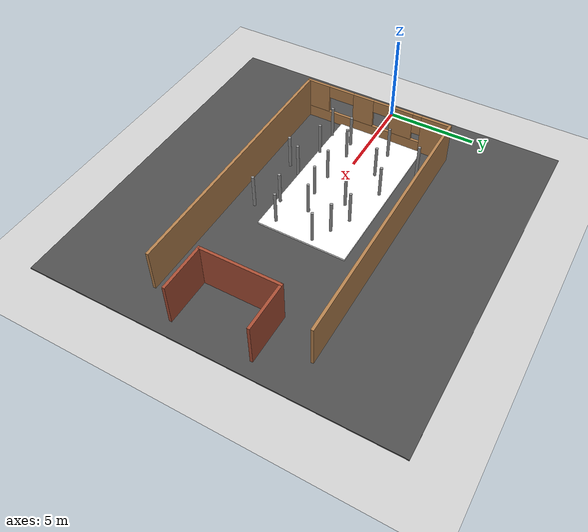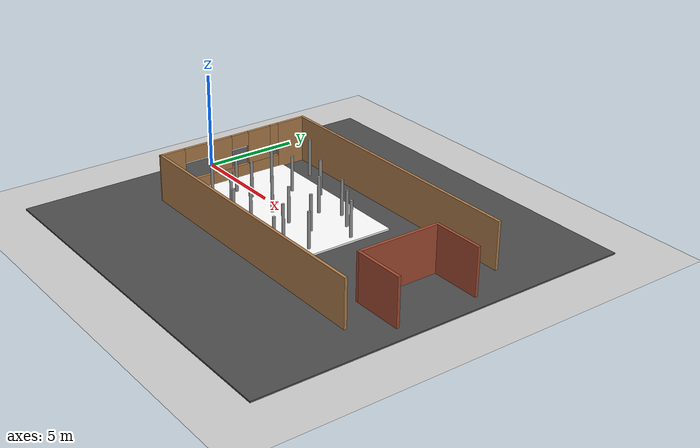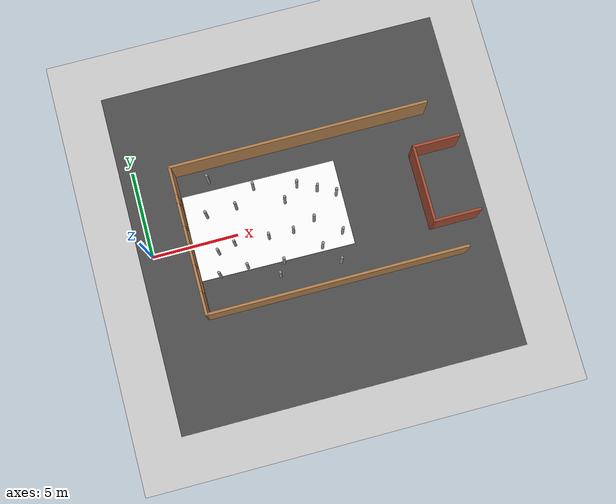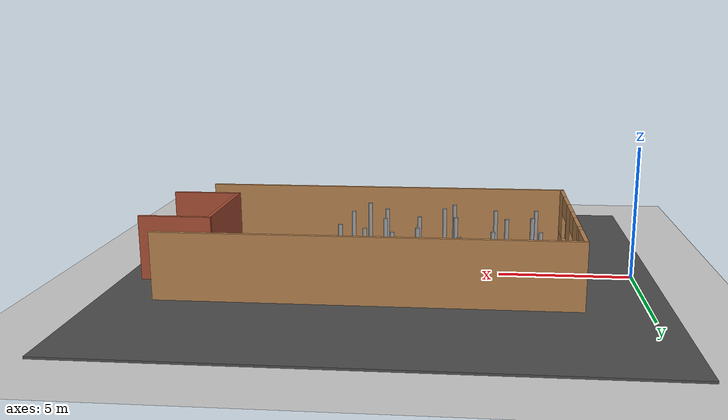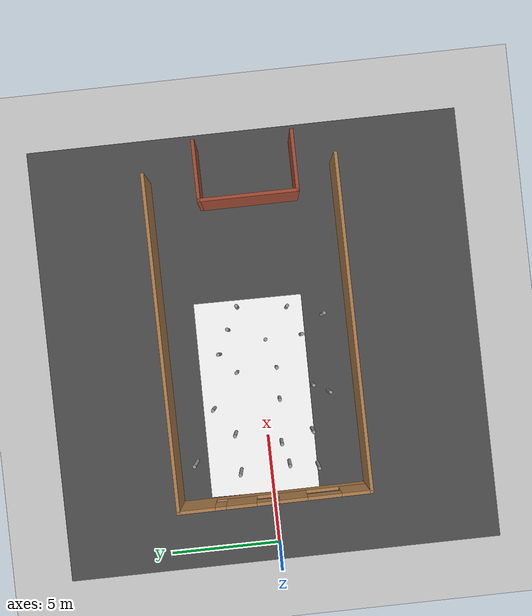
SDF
<sdf version="1.6">
 <world name="default">
  <model name="ground_plane">
   <static>1</static>
   <link name="link">
    <collision name="collision">
     <geometry><plane><normal>0 0 1</normal><size>100 100</size></plane></geometry>
     <surface><friction><ode><mu>100</mu><mu2>50</mu2></ode></friction></surface>
    </collision>
    <visual name="visual">
     <cast_shadows>0</cast_shadows>
     <geometry><plane><normal>0 0 1</normal><size>100 100</size></plane></geometry>
     <material>
      <script><uri>file://media/materials/scripts/gazebo.material</uri><name>Gazebo/Grey</name></script>
     </material>
    </visual>
   </link>
  </model>
  <gravity>0 0 -9.8</gravity>
  <magnetic_field>6e-06 2.3e-05 -4.2e-05</magnetic_field>
  <atmosphere type="adiabatic"/>
  <physics name="default_physics" default="0" type="ode">
   <max_step_size>0.001</max_step_size>
   <real_time_factor>1</real_time_factor>
   <real_time_update_rate>1000</real_time_update_rate>
  </physics>
  <scene><ambient>0.4 0.4 0.4 1</ambient><background>0.7 0.7 0.7 1</background><shadows>1</shadows></scene>
  <spherical_coordinates>
   <surface_model>EARTH_WGS84</surface_model>
   <latitude_deg>0</latitude_deg>
   <longitude_deg>0</longitude_deg>
   <elevation>0</elevation>
   <heading_deg>0</heading_deg>
  </spherical_coordinates>
  <model name="poste_16x200_clone_6_clone_9">
   <link name="link_1">
    <inertial>
     <mass>1</mass>
     <inertia><ixx>0.145833</ixx><ixy>0</ixy><ixz>0</ixz><iyy>0.145833</iyy><iyz>0</iyz><izz>0.125</izz></inertia>
    </inertial>
    <pose>5e-06 3e-06 0 0 -0 0</pose>
    <visual name="visual">
     <geometry><cylinder><radius>0.08</radius><length>2</length></cylinder></geometry>
     <material>
      <lighting>1</lighting>
      <script><uri>file://media/materials/scripts/gazebo.material</uri><name>Gazebo/Grey</name></script>
      <shader type="vertex"><normal_map>__default__</normal_map></shader>
      <ambient>0.3 0.3 0.3 1</ambient>
      <diffuse>0.7 0.7 0.7 1</diffuse>
      <specular>0.01 0.01 0.01 1</specular>
      <emissive>0 0 0 1</emissive>
     </material>
    </visual>
    <collision name="collision">
     <geometry><cylinder><radius>0.08</radius><length>2</length></cylinder></geometry>
     <surface>
      <friction>
       <ode><mu>1</mu><mu2>1</mu2><fdir1>0 0 0</fdir1><slip1>0</slip1><slip2>0</slip2></ode>
       <torsional>
        <coefficient>1</coefficient>
        <patch_radius>0</patch_radius>
        <surface_radius>0</surface_radius>
        <use_patch_radius>1</use_patch_radius>
        <ode><slip>0</slip></ode>
       </torsional>
      </friction>
      <bounce><restitution_coefficient>0</restitution_coefficient><threshold>1e+06</threshold></bounce>
      <contact>
       <collide_without_contact>0</collide_without_contact>
       <collide_without_contact_bitmask>1</collide_without_contact_bitmask>
       <collide_bitmask>1</collide_bitmask>
       <ode>
        <soft_cfm>0</soft_cfm>
        <soft_erp>0.2</soft_erp>
        <kp>1e+13</kp>
        <kd>1</kd>
        <max_vel>0.01</max_vel>
        <min_depth>0</min_depth>
       </ode>
       <bullet>
        <split_impulse>1</split_impulse>
        <split_impulse_penetration_threshold>-0.01</split_impulse_penetration_threshold>
        <soft_cfm>0</soft_cfm>
        <soft_erp>0.2</soft_erp>
        <kp>1e+13</kp>
        <kd>1</kd>
       </bullet>
      </contact>
     </surface>
    </collision>
   </link>
   <static>0</static>
   <pose>6.7957 -2.95609 1.05 -6.3e-05 3e-05 -0.033285</pose>
  </model>
  <model name="poste_16x200_clone_6_clone_14">
   <link name="link_1">
    <inertial>
     <mass>1</mass>
     <inertia><ixx>0.145833</ixx><ixy>0</ixy><ixz>0</ixz><iyy>0.145833</iyy><iyz>0</iyz><izz>0.125</izz></inertia>
    </inertial>
    <pose>5e-06 3e-06 0 0 -0 0</pose>
    <visual name="visual">
     <geometry><cylinder><radius>0.08</radius><length>2</length></cylinder></geometry>
     <material>
      <lighting>1</lighting>
      <script><uri>file://media/materials/scripts/gazebo.material</uri><name>Gazebo/Grey</name></script>
      <shader type="vertex"><normal_map>__default__</normal_map></shader>
      <ambient>0.3 0.3 0.3 1</ambient>
      <diffuse>0.7 0.7 0.7 1</diffuse>
      <specular>0.01 0.01 0.01 1</specular>
      <emissive>0 0 0 1</emissive>
     </material>
    </visual>
    <collision name="collision">
     <geometry><cylinder><radius>0.08</radius><length>2</length></cylinder></geometry>
     <surface>
      <friction>
       <ode><mu>1</mu><mu2>1</mu2><fdir1>0 0 0</fdir1><slip1>0</slip1><slip2>0</slip2></ode>
       <torsional>
        <coefficient>1</coefficient>
        <patch_radius>0</patch_radius>
        <surface_radius>0</surface_radius>
        <use_patch_radius>1</use_patch_radius>
        <ode><slip>0</slip></ode>
       </torsional>
      </friction>
      <bounce><restitution_coefficient>0</restitution_coefficient><threshold>1e+06</threshold></bounce>
      <contact>
       <collide_without_contact>0</collide_without_contact>
       <collide_without_contact_bitmask>1</collide_without_contact_bitmask>
       <collide_bitmask>1</collide_bitmask>
       <ode>
        <soft_cfm>0</soft_cfm>
        <soft_erp>0.2</soft_erp>
        <kp>1e+13</kp>
        <kd>1</kd>
        <max_vel>0.01</max_vel>
        <min_depth>0</min_depth>
       </ode>
       <bullet>
        <split_impulse>1</split_impulse>
        <split_impulse_penetration_threshold>-0.01</split_impulse_penetration_threshold>
        <soft_cfm>0</soft_cfm>
        <soft_erp>0.2</soft_erp>
        <kp>1e+13</kp>
        <kd>1</kd>
       </bullet>
      </contact>
     </surface>
    </collision>
   </link>
   <static>0</static>
   <pose>4.1574 3.37993 1.05 -7.5e-05 3.4e-05 -0.012222</pose>
  </model>
  <model name="poste_16x200_clone_6_clone_21">
   <link name="link_1">
    <inertial>
     <mass>1</mass>
     <inertia><ixx>0.145833</ixx><ixy>0</ixy><ixz>0</ixz><iyy>0.145833</iyy><iyz>0</iyz><izz>0.125</izz></inertia>
    </inertial>
    <pose>5e-06 3e-06 0 0 -0 0</pose>
    <visual name="visual">
     <geometry><cylinder><radius>0.08</radius><length>2</length></cylinder></geometry>
     <material>
      <lighting>1</lighting>
      <script><uri>file://media/materials/scripts/gazebo.material</uri><name>Gazebo/Grey</name></script>
      <shader type="vertex"><normal_map>__default__</normal_map></shader>
      <ambient>0.3 0.3 0.3 1</ambient>
      <diffuse>0.7 0.7 0.7 1</diffuse>
      <specular>0.01 0.01 0.01 1</specular>
      <emissive>0 0 0 1</emissive>
     </material>
    </visual>
    <collision name="collision">
     <geometry><cylinder><radius>0.08</radius><length>2</length></cylinder></geometry>
     <surface>
      <friction>
       <ode><mu>1</mu><mu2>1</mu2><fdir1>0 0 0</fdir1><slip1>0</slip1><slip2>0</slip2></ode>
       <torsional>
        <coefficient>1</coefficient>
        <patch_radius>0</patch_radius>
        <surface_radius>0</surface_radius>
        <use_patch_radius>1</use_patch_radius>
        <ode><slip>0</slip></ode>
       </torsional>
      </friction>
      <bounce><restitution_coefficient>0</restitution_coefficient><threshold>1e+06</threshold></bounce>
      <contact>
       <collide_without_contact>0</collide_without_contact>
       <collide_without_contact_bitmask>1</collide_without_contact_bitmask>
       <collide_bitmask>1</collide_bitmask>
       <ode>
        <soft_cfm>0</soft_cfm>
        <soft_erp>0.2</soft_erp>
        <kp>1e+13</kp>
        <kd>1</kd>
        <max_vel>0.01</max_vel>
        <min_depth>0</min_depth>
       </ode>
       <bullet>
        <split_impulse>1</split_impulse>
        <split_impulse_penetration_threshold>-0.01</split_impulse_penetration_threshold>
        <soft_cfm>0</soft_cfm>
        <soft_erp>0.2</soft_erp>
        <kp>1e+13</kp>
        <kd>1</kd>
       </bullet>
      </contact>
     </surface>
    </collision>
   </link>
   <static>0</static>
   <pose>10.3112 -3.04353 1.05001 -6.3e-05 2.9e-05 -0.033665</pose>
  </model>
  <model name="asphalt_plane">
   <static>1</static>
   <link name="link">
    <collision name="collision"><geometry><box><size>20 20 0.1</size></box></geometry></collision>
    <visual name="visual">
     <cast_shadows>0</cast_shadows>
     <geometry><box><size>20 20 0.1</size></box></geometry>
     <material>
      <script>
       <uri>model://asphalt_plane/materials/scripts</uri>
       <uri>model://asphalt_plane/materials/textures</uri>
       <name>vrc/asphalt</name>
      </script>
     </material>
    </visual>
   </link>
   <pose>9.20899 -0.21691 0 0 -0 0</pose>
  </model>
  <model name="janelas">
   <link name="Wall_0">
    <pose>-8.0218 -0.020049 0 0 0 -1.56601</pose>
    <inertial>
     <mass>1</mass>
     <inertia><ixx>1</ixx><ixy>0</ixy><ixz>0</ixz><iyy>1</iyy><iyz>0</iyz><izz>1</izz></inertia>
    </inertial>
    <visual name="Wall_0_Visual_0">
     <pose>-3.4811 0 1.25 0 -0 0</pose>
     <geometry><box><size>1.64474 0.15 2.5</size></box></geometry>
     <material>
      <script><uri>file://media/materials/scripts/gazebo.material</uri><name>Gazebo/Wood</name></script>
      <ambient>1 1 1 1</ambient>
      <shader type="pixel"><normal_map>__default__</normal_map></shader>
      <diffuse>1 1 1 1</diffuse>
      <specular>0.2 0.2 0.2 1</specular>
      <emissive>0 0 0 1</emissive>
     </material>
     <meta><layer>0</layer></meta>
    </visual>
    <visual name="Wall_0_Visual_1">
     <pose>0.822368 0 0.375 0 -0 0</pose>
     <geometry><box><size>6.96219 0.15 0.75</size></box></geometry>
     <material>
      <script><uri>file://media/materials/scripts/gazebo.material</uri><name>Gazebo/Wood</name></script>
      <ambient>1 1 1 1</ambient>
      <shader type="pixel"><normal_map>__default__</normal_map></shader>
      <diffuse>1 1 1 1</diffuse>
      <specular>0.2 0.2 0.2 1</specular>
      <emissive>0 0 0 1</emissive>
     </material>
     <meta><layer>0</layer></meta>
    </visual>
    <visual name="Wall_0_Visual_2">
     <pose>-1.48773 0 1.625 0 -0 0</pose>
     <geometry><box><size>1.342 0.15 1.75</size></box></geometry>
     <material>
      <script><uri>file://media/materials/scripts/gazebo.material</uri><name>Gazebo/Wood</name></script>
      <ambient>1 1 1 1</ambient>
      <shader type="pixel"><normal_map>__default__</normal_map></shader>
      <diffuse>1 1 1 1</diffuse>
      <specular>0.2 0.2 0.2 1</specular>
      <emissive>0 0 0 1</emissive>
     </material>
     <meta><layer>0</layer></meta>
    </visual>
    <visual name="Wall_0_Visual_3">
     <pose>0.800404 0 1.625 0 -0 0</pose>
     <geometry><box><size>1.23426 0.15 1.75</size></box></geometry>
     <material>
      <script><uri>file://media/materials/scripts/gazebo.material</uri><name>Gazebo/Wood</name></script>
      <ambient>1 1 1 1</ambient>
      <shader type="pixel"><normal_map>__default__</normal_map></shader>
      <diffuse>1 1 1 1</diffuse>
      <specular>0.2 0.2 0.2 1</specular>
      <emissive>0 0 0 1</emissive>
     </material>
     <meta><layer>0</layer></meta>
    </visual>
    <visual name="Wall_0_Visual_4">
     <pose>3.6105 0 1.625 0 -0 0</pose>
     <geometry><box><size>1.38593 0.15 1.75</size></box></geometry>
     <material>
      <script><uri>file://media/materials/scripts/gazebo.material</uri><name>Gazebo/Wood</name></script>
      <ambient>1 1 1 1</ambient>
      <shader type="pixel"><normal_map>__default__</normal_map></shader>
      <diffuse>1 1 1 1</diffuse>
      <specular>0.2 0.2 0.2 1</specular>
      <emissive>0 0 0 1</emissive>
     </material>
     <meta><layer>0</layer></meta>
    </visual>
    <visual name="Wall_0_Visual_5">
     <pose>-2.40873 0 1.875 0 -0 0</pose>
     <geometry><box><size>0.5 0.15 1.25</size></box></geometry>
     <material>
      <script><uri>file://media/materials/scripts/gazebo.material</uri><name>Gazebo/Wood</name></script>
      <ambient>1 1 1 1</ambient>
      <shader type="pixel"><normal_map>__default__</normal_map></shader>
      <diffuse>1 1 1 1</diffuse>
      <specular>0.2 0.2 0.2 1</specular>
      <emissive>0 0 0 1</emissive>
     </material>
     <meta><layer>0</layer></meta>
    </visual>
    <visual name="Wall_0_Visual_6">
     <pose>-0.316724 0 2.125 0 -0 0</pose>
     <geometry><box><size>1 0.15 0.75</size></box></geometry>
     <material>
      <script><uri>file://media/materials/scripts/gazebo.material</uri><name>Gazebo/Wood</name></script>
      <ambient>1 1 1 1</ambient>
      <shader type="pixel"><normal_map>__default__</normal_map></shader>
      <diffuse>1 1 1 1</diffuse>
      <specular>0.2 0.2 0.2 1</specular>
      <emissive>0 0 0 1</emissive>
     </material>
     <meta><layer>0</layer></meta>
    </visual>
    <visual name="Wall_0_Visual_7">
     <pose>2.16753 0 2.125 0 -0 0</pose>
     <geometry><box><size>1.5 0.15 0.75</size></box></geometry>
     <material>
      <script><uri>file://media/materials/scripts/gazebo.material</uri><name>Gazebo/Wood</name></script>
      <ambient>1 1 1 1</ambient>
      <shader type="pixel"><normal_map>__default__</normal_map></shader>
      <diffuse>1 1 1 1</diffuse>
      <specular>0.2 0.2 0.2 1</specular>
      <emissive>0 0 0 1</emissive>
     </material>
     <meta><layer>0</layer></meta>
    </visual>
    <collision name="Wall_0_Collision_0">
     <pose>-3.4811 0 1.25 0 -0 0</pose>
     <geometry><box><size>1.64474 0.15 2.5</size></box></geometry>
     <surface>
      <friction>
       <ode><mu>1</mu><mu2>1</mu2><fdir1>0 0 0</fdir1><slip1>0</slip1><slip2>0</slip2></ode>
       <torsional>
        <coefficient>1</coefficient>
        <patch_radius>0</patch_radius>
        <surface_radius>0</surface_radius>
        <use_patch_radius>1</use_patch_radius>
        <ode><slip>0</slip></ode>
       </torsional>
      </friction>
      <bounce><restitution_coefficient>0</restitution_coefficient><threshold>1e+06</threshold></bounce>
      <contact>
       <collide_without_contact>0</collide_without_contact>
       <collide_without_contact_bitmask>1</collide_without_contact_bitmask>
       <collide_bitmask>1</collide_bitmask>
       <ode>
        <soft_cfm>0</soft_cfm>
        <soft_erp>0.2</soft_erp>
        <kp>1e+13</kp>
        <kd>1</kd>
        <max_vel>0.01</max_vel>
        <min_depth>0</min_depth>
       </ode>
       <bullet>
        <split_impulse>1</split_impulse>
        <split_impulse_penetration_threshold>-0.01</split_impulse_penetration_threshold>
        <soft_cfm>0</soft_cfm>
        <soft_erp>0.2</soft_erp>
        <kp>1e+13</kp>
        <kd>1</kd>
       </bullet>
      </contact>
     </surface>
    </collision>
    <collision name="Wall_0_Collision_1">
     <pose>0.822368 0 0.375 0 -0 0</pose>
     <geometry><box><size>6.96219 0.15 0.75</size></box></geometry>
     <surface>
      <friction>
       <ode><mu>1</mu><mu2>1</mu2><fdir1>0 0 0</fdir1><slip1>0</slip1><slip2>0</slip2></ode>
       <torsional>
        <coefficient>1</coefficient>
        <patch_radius>0</patch_radius>
        <surface_radius>0</surface_radius>
        <use_patch_radius>1</use_patch_radius>
        <ode><slip>0</slip></ode>
       </torsional>
      </friction>
      <bounce><restitution_coefficient>0</restitution_coefficient><threshold>1e+06</threshold></bounce>
      <contact>
       <collide_without_contact>0</collide_without_contact>
       <collide_without_contact_bitmask>1</collide_without_contact_bitmask>
       <collide_bitmask>1</collide_bitmask>
       <ode>
        <soft_cfm>0</soft_cfm>
        <soft_erp>0.2</soft_erp>
        <kp>1e+13</kp>
        <kd>1</kd>
        <max_vel>0.01</max_vel>
        <min_depth>0</min_depth>
       </ode>
       <bullet>
        <split_impulse>1</split_impulse>
        <split_impulse_penetration_threshold>-0.01</split_impulse_penetration_threshold>
        <soft_cfm>0</soft_cfm>
        <soft_erp>0.2</soft_erp>
        <kp>1e+13</kp>
        <kd>1</kd>
       </bullet>
      </contact>
     </surface>
    </collision>
    <collision name="Wall_0_Collision_2">
     <pose>-1.48773 0 1.625 0 -0 0</pose>
     <geometry><box><size>1.342 0.15 1.75</size></box></geometry>
     <surface>
      <friction>
       <ode><mu>1</mu><mu2>1</mu2><fdir1>0 0 0</fdir1><slip1>0</slip1><slip2>0</slip2></ode>
       <torsional>
        <coefficient>1</coefficient>
        <patch_radius>0</patch_radius>
        <surface_radius>0</surface_radius>
        <use_patch_radius>1</use_patch_radius>
        <ode><slip>0</slip></ode>
       </torsional>
      </friction>
      <bounce><restitution_coefficient>0</restitution_coefficient><threshold>1e+06</threshold></bounce>
      <contact>
       <collide_without_contact>0</collide_without_contact>
       <collide_without_contact_bitmask>1</collide_without_contact_bitmask>
       <collide_bitmask>1</collide_bitmask>
       <ode>
        <soft_cfm>0</soft_cfm>
        <soft_erp>0.2</soft_erp>
        <kp>1e+13</kp>
        <kd>1</kd>
        <max_vel>0.01</max_vel>
        <min_depth>0</min_depth>
       </ode>
       <bullet>
        <split_impulse>1</split_impulse>
        <split_impulse_penetration_threshold>-0.01</split_impulse_penetration_threshold>
        <soft_cfm>0</soft_cfm>
        <soft_erp>0.2</soft_erp>
        <kp>1e+13</kp>
        <kd>1</kd>
       </bullet>
      </contact>
     </surface>
    </collision>
    <collision name="Wall_0_Collision_4">
     <pose>3.6105 0 1.625 0 -0 0</pose>
     <geometry><box><size>1.38593 0.15 1.75</size></box></geometry>
     <surface>
      <friction>
       <ode><mu>1</mu><mu2>1</mu2><fdir1>0 0 0</fdir1><slip1>0</slip1><slip2>0</slip2></ode>
       <torsional>
        <coefficient>1</coefficient>
        <patch_radius>0</patch_radius>
        <surface_radius>0</surface_radius>
        <use_patch_radius>1</use_patch_radius>
        <ode><slip>0</slip></ode>
       </torsional>
      </friction>
      <bounce><restitution_coefficient>0</restitution_coefficient><threshold>1e+06</threshold></bounce>
      <contact>
       <collide_without_contact>0</collide_without_contact>
       <collide_without_contact_bitmask>1</collide_without_contact_bitmask>
       <collide_bitmask>1</collide_bitmask>
       <ode>
        <soft_cfm>0</soft_cfm>
        <soft_erp>0.2</soft_erp>
        <kp>1e+13</kp>
        <kd>1</kd>
        <max_vel>0.01</max_vel>
        <min_depth>0</min_depth>
       </ode>
       <bullet>
        <split_impulse>1</split_impulse>
        <split_impulse_penetration_threshold>-0.01</split_impulse_penetration_threshold>
        <soft_cfm>0</soft_cfm>
        <soft_erp>0.2</soft_erp>
        <kp>1e+13</kp>
        <kd>1</kd>
       </bullet>
      </contact>
     </surface>
    </collision>
    <collision name="Wall_0_Collision_3">
     <pose>0.800404 0 1.625 0 -0 0</pose>
     <geometry><box><size>1.23426 0.15 1.75</size></box></geometry>
     <surface>
      <friction>
       <ode><mu>1</mu><mu2>1</mu2><fdir1>0 0 0</fdir1><slip1>0</slip1><slip2>0</slip2></ode>
       <torsional>
        <coefficient>1</coefficient>
        <patch_radius>0</patch_radius>
        <surface_radius>0</surface_radius>
        <use_patch_radius>1</use_patch_radius>
        <ode><slip>0</slip></ode>
       </torsional>
      </friction>
      <bounce><restitution_coefficient>0</restitution_coefficient><threshold>1e+06</threshold></bounce>
      <contact>
       <collide_without_contact>0</collide_without_contact>
       <collide_without_contact_bitmask>1</collide_without_contact_bitmask>
       <collide_bitmask>1</collide_bitmask>
       <ode>
        <soft_cfm>0</soft_cfm>
        <soft_erp>0.2</soft_erp>
        <kp>1e+13</kp>
        <kd>1</kd>
        <max_vel>0.01</max_vel>
        <min_depth>0</min_depth>
       </ode>
       <bullet>
        <split_impulse>1</split_impulse>
        <split_impulse_penetration_threshold>-0.01</split_impulse_penetration_threshold>
        <soft_cfm>0</soft_cfm>
        <soft_erp>0.2</soft_erp>
        <kp>1e+13</kp>
        <kd>1</kd>
       </bullet>
      </contact>
     </surface>
    </collision>
    <collision name="Wall_0_Collision_5">
     <pose>-2.40873 0 1.875 0 -0 0</pose>
     <geometry><box><size>0.5 0.15 1.25</size></box></geometry>
     <surface>
      <friction>
       <ode><mu>1</mu><mu2>1</mu2><fdir1>0 0 0</fdir1><slip1>0</slip1><slip2>0</slip2></ode>
       <torsional>
        <coefficient>1</coefficient>
        <patch_radius>0</patch_radius>
        <surface_radius>0</surface_radius>
        <use_patch_radius>1</use_patch_radius>
        <ode><slip>0</slip></ode>
       </torsional>
      </friction>
      <bounce><restitution_coefficient>0</restitution_coefficient><threshold>1e+06</threshold></bounce>
      <contact>
       <collide_without_contact>0</collide_without_contact>
       <collide_without_contact_bitmask>1</collide_without_contact_bitmask>
       <collide_bitmask>1</collide_bitmask>
       <ode>
        <soft_cfm>0</soft_cfm>
        <soft_erp>0.2</soft_erp>
        <kp>1e+13</kp>
        <kd>1</kd>
        <max_vel>0.01</max_vel>
        <min_depth>0</min_depth>
       </ode>
       <bullet>
        <split_impulse>1</split_impulse>
        <split_impulse_penetration_threshold>-0.01</split_impulse_penetration_threshold>
        <soft_cfm>0</soft_cfm>
        <soft_erp>0.2</soft_erp>
        <kp>1e+13</kp>
        <kd>1</kd>
       </bullet>
      </contact>
     </surface>
    </collision>
    <collision name="Wall_0_Collision_6">
     <pose>-0.316724 0 2.125 0 -0 0</pose>
     <geometry><box><size>1 0.15 0.75</size></box></geometry>
     <surface>
      <friction>
       <ode><mu>1</mu><mu2>1</mu2><fdir1>0 0 0</fdir1><slip1>0</slip1><slip2>0</slip2></ode>
       <torsional>
        <coefficient>1</coefficient>
        <patch_radius>0</patch_radius>
        <surface_radius>0</surface_radius>
        <use_patch_radius>1</use_patch_radius>
        <ode><slip>0</slip></ode>
       </torsional>
      </friction>
      <bounce><restitution_coefficient>0</restitution_coefficient><threshold>1e+06</threshold></bounce>
      <contact>
       <collide_without_contact>0</collide_without_contact>
       <collide_without_contact_bitmask>1</collide_without_contact_bitmask>
       <collide_bitmask>1</collide_bitmask>
       <ode>
        <soft_cfm>0</soft_cfm>
        <soft_erp>0.2</soft_erp>
        <kp>1e+13</kp>
        <kd>1</kd>
        <max_vel>0.01</max_vel>
        <min_depth>0</min_depth>
       </ode>
       <bullet>
        <split_impulse>1</split_impulse>
        <split_impulse_penetration_threshold>-0.01</split_impulse_penetration_threshold>
        <soft_cfm>0</soft_cfm>
        <soft_erp>0.2</soft_erp>
        <kp>1e+13</kp>
        <kd>1</kd>
       </bullet>
      </contact>
     </surface>
    </collision>
    <collision name="Wall_0_Collision_7">
     <pose>2.16753 0 2.125 0 -0 0</pose>
     <geometry><box><size>1.5 0.15 0.75</size></box></geometry>
     <surface>
      <friction>
       <ode><mu>1</mu><mu2>1</mu2><fdir1>0 0 0</fdir1><slip1>0</slip1><slip2>0</slip2></ode>
       <torsional>
        <coefficient>1</coefficient>
        <patch_radius>0</patch_radius>
        <surface_radius>0</surface_radius>
        <use_patch_radius>1</use_patch_radius>
        <ode><slip>0</slip></ode>
       </torsional>
      </friction>
      <bounce><restitution_coefficient>0</restitution_coefficient><threshold>1e+06</threshold></bounce>
      <contact>
       <collide_without_contact>0</collide_without_contact>
       <collide_without_contact_bitmask>1</collide_without_contact_bitmask>
       <collide_bitmask>1</collide_bitmask>
       <ode>
        <soft_cfm>0</soft_cfm>
        <soft_erp>0.2</soft_erp>
        <kp>1e+13</kp>
        <kd>1</kd>
        <max_vel>0.01</max_vel>
        <min_depth>0</min_depth>
       </ode>
       <bullet>
        <split_impulse>1</split_impulse>
        <split_impulse_penetration_threshold>-0.01</split_impulse_penetration_threshold>
        <soft_cfm>0</soft_cfm>
        <soft_erp>0.2</soft_erp>
        <kp>1e+13</kp>
        <kd>1</kd>
       </bullet>
      </contact>
     </surface>
    </collision>
   </link>
   <link name="Wall_1">
    <pose>-0.576571 -4.24847 0 0 -0 0</pose>
    <inertial>
     <mass>1</mass>
     <inertia><ixx>1</ixx><ixy>0</ixy><ixz>0</ixz><iyy>1</iyy><iyz>0</iyz><izz>1</izz></inertia>
    </inertial>
    <visual name="Wall_1_Visual">
     <pose>0 0 1.25 0 -0 0</pose>
     <geometry><box><size>15 0.15 2.5</size></box></geometry>
     <material>
      <script><uri>file://media/materials/scripts/gazebo.material</uri><name>Gazebo/Wood</name></script>
      <ambient>1 1 1 1</ambient>
      <shader type="pixel"><normal_map>__default__</normal_map></shader>
      <diffuse>1 1 1 1</diffuse>
      <specular>0.2 0.2 0.2 1</specular>
      <emissive>0 0 0 1</emissive>
     </material>
     <meta><layer>0</layer></meta>
    </visual>
    <collision name="Wall_1_Collision">
     <pose>0 0 1.25 0 -0 0</pose>
     <geometry><box><size>15 0.15 2.5</size></box></geometry>
     <surface>
      <friction>
       <ode><mu>1</mu><mu2>1</mu2><fdir1>0 0 0</fdir1><slip1>0</slip1><slip2>0</slip2></ode>
       <torsional>
        <coefficient>1</coefficient>
        <patch_radius>0</patch_radius>
        <surface_radius>0</surface_radius>
        <use_patch_radius>1</use_patch_radius>
        <ode><slip>0</slip></ode>
       </torsional>
      </friction>
      <bounce><restitution_coefficient>0</restitution_coefficient><threshold>1e+06</threshold></bounce>
      <contact>
       <collide_without_contact>0</collide_without_contact>
       <collide_without_contact_bitmask>1</collide_without_contact_bitmask>
       <collide_bitmask>1</collide_bitmask>
       <ode>
        <soft_cfm>0</soft_cfm>
        <soft_erp>0.2</soft_erp>
        <kp>1e+13</kp>
        <kd>1</kd>
        <max_vel>0.01</max_vel>
        <min_depth>0</min_depth>
       </ode>
       <bullet>
        <split_impulse>1</split_impulse>
        <split_impulse_penetration_threshold>-0.01</split_impulse_penetration_threshold>
        <soft_cfm>0</soft_cfm>
        <soft_erp>0.2</soft_erp>
        <kp>1e+13</kp>
        <kd>1</kd>
       </bullet>
      </contact>
     </surface>
    </collision>
   </link>
   <link name="Wall_11">
    <pose>6.74238 1.9124 0 0 -0 0</pose>
    <visual name="Wall_11_Visual">
     <pose>0 0 1.25 0 -0 0</pose>
     <geometry><box><size>2.75 0.15 2.5</size></box></geometry>
     <material>
      <script><uri>file://media/materials/scripts/gazebo.material</uri><name>Gazebo/Bricks</name></script>
      <ambient>1 1 1 1</ambient>
      <shader type="pixel"/>
      <diffuse>1 1 1 1</diffuse>
      <specular>0.2 0.2 0.2 1</specular>
      <emissive>0 0 0 1</emissive>
     </material>
     <meta><layer>0</layer></meta>
    </visual>
    <collision name="Wall_11_Collision">
     <pose>0 0 1.25 0 -0 0</pose>
     <geometry><box><size>2.75 0.15 2.5</size></box></geometry>
     <surface>
      <friction>
       <ode><mu>1</mu><mu2>1</mu2><fdir1>0 0 0</fdir1><slip1>0</slip1><slip2>0</slip2></ode>
       <torsional>
        <coefficient>1</coefficient>
        <patch_radius>0</patch_radius>
        <surface_radius>0</surface_radius>
        <use_patch_radius>1</use_patch_radius>
        <ode><slip>0</slip></ode>
       </torsional>
      </friction>
      <bounce><restitution_coefficient>0</restitution_coefficient><threshold>1e+06</threshold></bounce>
      <contact>
       <collide_without_contact>0</collide_without_contact>
       <collide_without_contact_bitmask>1</collide_without_contact_bitmask>
       <collide_bitmask>1</collide_bitmask>
       <ode>
        <soft_cfm>0</soft_cfm>
        <soft_erp>0.2</soft_erp>
        <kp>1e+13</kp>
        <kd>1</kd>
        <max_vel>0.01</max_vel>
        <min_depth>0</min_depth>
       </ode>
       <bullet>
        <split_impulse>1</split_impulse>
        <split_impulse_penetration_threshold>-0.01</split_impulse_penetration_threshold>
        <soft_cfm>0</soft_cfm>
        <soft_erp>0.2</soft_erp>
        <kp>1e+13</kp>
        <kd>1</kd>
       </bullet>
      </contact>
     </surface>
    </collision>
   </link>
   <link name="Wall_3">
    <pose>-0.617027 4.24882 0 0 -0 0</pose>
    <inertial>
     <mass>1</mass>
     <inertia><ixx>1</ixx><ixy>0</ixy><ixz>0</ixz><iyy>1</iyy><iyz>0</iyz><izz>1</izz></inertia>
    </inertial>
    <visual name="Wall_3_Visual">
     <pose>0 0 1.25 0 -0 0</pose>
     <geometry><box><size>15 0.15 2.5</size></box></geometry>
     <material>
      <script><uri>file://media/materials/scripts/gazebo.material</uri><name>Gazebo/Wood</name></script>
      <ambient>1 1 1 1</ambient>
      <shader type="pixel"><normal_map>__default__</normal_map></shader>
      <diffuse>1 1 1 1</diffuse>
      <specular>0.2 0.2 0.2 1</specular>
      <emissive>0 0 0 1</emissive>
     </material>
     <meta><layer>0</layer></meta>
    </visual>
    <collision name="Wall_3_Collision">
     <pose>0 0 1.25 0 -0 0</pose>
     <geometry><box><size>15 0.15 2.5</size></box></geometry>
     <surface>
      <friction>
       <ode><mu>1</mu><mu2>1</mu2><fdir1>0 0 0</fdir1><slip1>0</slip1><slip2>0</slip2></ode>
       <torsional>
        <coefficient>1</coefficient>
        <patch_radius>0</patch_radius>
        <surface_radius>0</surface_radius>
        <use_patch_radius>1</use_patch_radius>
        <ode><slip>0</slip></ode>
       </torsional>
      </friction>
      <bounce><restitution_coefficient>0</restitution_coefficient><threshold>1e+06</threshold></bounce>
      <contact>
       <collide_without_contact>0</collide_without_contact>
       <collide_without_contact_bitmask>1</collide_without_contact_bitmask>
       <collide_bitmask>1</collide_bitmask>
       <ode>
        <soft_cfm>0</soft_cfm>
        <soft_erp>0.2</soft_erp>
        <kp>1e+13</kp>
        <kd>1</kd>
        <max_vel>0.01</max_vel>
        <min_depth>0</min_depth>
       </ode>
       <bullet>
        <split_impulse>1</split_impulse>
        <split_impulse_penetration_threshold>-0.01</split_impulse_penetration_threshold>
        <soft_cfm>0</soft_cfm>
        <soft_erp>0.2</soft_erp>
        <kp>1e+13</kp>
        <kd>1</kd>
       </bullet>
      </contact>
     </surface>
    </collision>
   </link>
   <link name="Wall_8">
    <pose>5.44238 -0.262605 0 0 0 -1.5708</pose>
    <inertial>
     <mass>1</mass>
     <inertia><ixx>1</ixx><ixy>0</ixy><ixz>0</ixz><iyy>1</iyy><iyz>0</iyz><izz>1</izz></inertia>
    </inertial>
    <visual name="Wall_8_Visual">
     <pose>0 0 1.25 0 -0 0</pose>
     <geometry><box><size>4.5 0.15 2.5</size></box></geometry>
     <material>
      <script><uri>file://media/materials/scripts/gazebo.material</uri><name>Gazebo/Bricks</name></script>
      <ambient>1 1 1 1</ambient>
      <shader type="pixel"><normal_map>__default__</normal_map></shader>
      <diffuse>1 1 1 1</diffuse>
      <specular>0.2 0.2 0.2 1</specular>
      <emissive>0 0 0 1</emissive>
     </material>
     <meta><layer>0</layer></meta>
    </visual>
    <collision name="Wall_8_Collision">
     <pose>0 0 1.25 0 -0 0</pose>
     <geometry><box><size>4.5 0.15 2.5</size></box></geometry>
     <surface>
      <friction>
       <ode><mu>1</mu><mu2>1</mu2><fdir1>0 0 0</fdir1><slip1>0</slip1><slip2>0</slip2></ode>
       <torsional>
        <coefficient>1</coefficient>
        <patch_radius>0</patch_radius>
        <surface_radius>0</surface_radius>
        <use_patch_radius>1</use_patch_radius>
        <ode><slip>0</slip></ode>
       </torsional>
      </friction>
      <bounce><restitution_coefficient>0</restitution_coefficient><threshold>1e+06</threshold></bounce>
      <contact>
       <collide_without_contact>0</collide_without_contact>
       <collide_without_contact_bitmask>1</collide_without_contact_bitmask>
       <collide_bitmask>1</collide_bitmask>
       <ode>
        <soft_cfm>0</soft_cfm>
        <soft_erp>0.2</soft_erp>
        <kp>1e+13</kp>
        <kd>1</kd>
        <max_vel>0.01</max_vel>
        <min_depth>0</min_depth>
       </ode>
       <bullet>
        <split_impulse>1</split_impulse>
        <split_impulse_penetration_threshold>-0.01</split_impulse_penetration_threshold>
        <soft_cfm>0</soft_cfm>
        <soft_erp>0.2</soft_erp>
        <kp>1e+13</kp>
        <kd>1</kd>
       </bullet>
      </contact>
     </surface>
    </collision>
   </link>
   <link name="Wall_9">
    <pose>6.74238 -2.4376 0 0 -0 0</pose>
    <visual name="Wall_9_Visual">
     <pose>0 0 1.25 0 -0 0</pose>
     <geometry><box><size>2.75 0.15 2.5</size></box></geometry>
     <material>
      <script><uri>file://media/materials/scripts/gazebo.material</uri><name>Gazebo/Bricks</name></script>
      <ambient>1 1 1 1</ambient>
      <shader type="pixel"/>
      <diffuse>1 1 1 1</diffuse>
      <specular>0.2 0.2 0.2 1</specular>
      <emissive>0 0 0 1</emissive>
     </material>
     <meta><layer>0</layer></meta>
    </visual>
    <collision name="Wall_9_Collision">
     <pose>0 0 1.25 0 -0 0</pose>
     <geometry><box><size>2.75 0.15 2.5</size></box></geometry>
     <surface>
      <friction>
       <ode><mu>1</mu><mu2>1</mu2><fdir1>0 0 0</fdir1><slip1>0</slip1><slip2>0</slip2></ode>
       <torsional>
        <coefficient>1</coefficient>
        <patch_radius>0</patch_radius>
        <surface_radius>0</surface_radius>
        <use_patch_radius>1</use_patch_radius>
        <ode><slip>0</slip></ode>
       </torsional>
      </friction>
      <bounce><restitution_coefficient>0</restitution_coefficient><threshold>1e+06</threshold></bounce>
      <contact>
       <collide_without_contact>0</collide_without_contact>
       <collide_without_contact_bitmask>1</collide_without_contact_bitmask>
       <collide_bitmask>1</collide_bitmask>
       <ode>
        <soft_cfm>0</soft_cfm>
        <soft_erp>0.2</soft_erp>
        <kp>1e+13</kp>
        <kd>1</kd>
        <max_vel>0.01</max_vel>
        <min_depth>0</min_depth>
       </ode>
       <bullet>
        <split_impulse>1</split_impulse>
        <split_impulse_penetration_threshold>-0.01</split_impulse_penetration_threshold>
        <soft_cfm>0</soft_cfm>
        <soft_erp>0.2</soft_erp>
        <kp>1e+13</kp>
        <kd>1</kd>
       </bullet>
      </contact>
     </surface>
    </collision>
   </link>
   <static>1</static>
   <pose>10.3261 0.006666 0 0 -0 0</pose>
  </model>
  <light name="sun_clone" type="directional">
   <pose>12.8161 -0.237466 10 0 -0 0</pose>
   <diffuse>0.8 0.8 0.8 1</diffuse>
   <specular>0.2 0.2 0.2 1</specular>
   <direction>-0.483368 0.096674 -0.870063</direction>
   <attenuation>
    <range>1000</range>
    <constant>0.9</constant>
    <linear>0.01</linear>
    <quadratic>0.001</quadratic>
   </attenuation>
  </light>
  <model name="poste_16x200_clone_6_clone_9_clone">
   <link name="link_1">
    <inertial>
     <mass>1</mass>
     <inertia><ixx>0.145833</ixx><ixy>0</ixy><ixz>0</ixz><iyy>0.145833</iyy><iyz>0</iyz><izz>0.125</izz></inertia>
    </inertial>
    <pose>5e-06 3e-06 0 0 -0 0</pose>
    <visual name="visual">
     <geometry><cylinder><radius>0.08</radius><length>2</length></cylinder></geometry>
     <material>
      <lighting>1</lighting>
      <script><uri>file://media/materials/scripts/gazebo.material</uri><name>Gazebo/Grey</name></script>
      <shader type="vertex"><normal_map>__default__</normal_map></shader>
      <ambient>0.3 0.3 0.3 1</ambient>
      <diffuse>0.7 0.7 0.7 1</diffuse>
      <specular>0.01 0.01 0.01 1</specular>
      <emissive>0 0 0 1</emissive>
     </material>
    </visual>
    <collision name="collision">
     <geometry><cylinder><radius>0.08</radius><length>2</length></cylinder></geometry>
     <surface>
      <friction>
       <ode><mu>1</mu><mu2>1</mu2><fdir1>0 0 0</fdir1><slip1>0</slip1><slip2>0</slip2></ode>
       <torsional>
        <coefficient>1</coefficient>
        <patch_radius>0</patch_radius>
        <surface_radius>0</surface_radius>
        <use_patch_radius>1</use_patch_radius>
        <ode><slip>0</slip></ode>
       </torsional>
      </friction>
      <bounce><restitution_coefficient>0</restitution_coefficient><threshold>1e+06</threshold></bounce>
      <contact>
       <collide_without_contact>0</collide_without_contact>
       <collide_without_contact_bitmask>1</collide_without_contact_bitmask>
       <collide_bitmask>1</collide_bitmask>
       <ode>
        <soft_cfm>0</soft_cfm>
        <soft_erp>0.2</soft_erp>
        <kp>1e+13</kp>
        <kd>1</kd>
        <max_vel>0.01</max_vel>
        <min_depth>0</min_depth>
       </ode>
       <bullet>
        <split_impulse>1</split_impulse>
        <split_impulse_penetration_threshold>-0.01</split_impulse_penetration_threshold>
        <soft_cfm>0</soft_cfm>
        <soft_erp>0.2</soft_erp>
        <kp>1e+13</kp>
        <kd>1</kd>
       </bullet>
      </contact>
     </surface>
    </collision>
   </link>
   <static>0</static>
   <pose>5.31395 1.46112 1.05015 -0.001739 -0.000954 -0.073362</pose>
  </model>
  <model name="poste_16x200_clone_6_clone_9_clone_0">
   <link name="link_1">
    <inertial>
     <mass>1</mass>
     <inertia><ixx>0.145833</ixx><ixy>0</ixy><ixz>0</ixz><iyy>0.145833</iyy><iyz>0</iyz><izz>0.125</izz></inertia>
    </inertial>
    <pose>5e-06 3e-06 0 0 -0 0</pose>
    <visual name="visual">
     <geometry><cylinder><radius>0.08</radius><length>2</length></cylinder></geometry>
     <material>
      <lighting>1</lighting>
      <script><uri>file://media/materials/scripts/gazebo.material</uri><name>Gazebo/Grey</name></script>
      <shader type="vertex"><normal_map>__default__</normal_map></shader>
      <ambient>0.3 0.3 0.3 1</ambient>
      <diffuse>0.7 0.7 0.7 1</diffuse>
      <specular>0.01 0.01 0.01 1</specular>
      <emissive>0 0 0 1</emissive>
     </material>
    </visual>
    <collision name="collision">
     <geometry><cylinder><radius>0.08</radius><length>2</length></cylinder></geometry>
     <surface>
      <friction>
       <ode><mu>1</mu><mu2>1</mu2><fdir1>0 0 0</fdir1><slip1>0</slip1><slip2>0</slip2></ode>
       <torsional>
        <coefficient>1</coefficient>
        <patch_radius>0</patch_radius>
        <surface_radius>0</surface_radius>
        <use_patch_radius>1</use_patch_radius>
        <ode><slip>0</slip></ode>
       </torsional>
      </friction>
      <bounce><restitution_coefficient>0</restitution_coefficient><threshold>1e+06</threshold></bounce>
      <contact>
       <collide_without_contact>0</collide_without_contact>
       <collide_without_contact_bitmask>1</collide_without_contact_bitmask>
       <collide_bitmask>1</collide_bitmask>
       <ode>
        <soft_cfm>0</soft_cfm>
        <soft_erp>0.2</soft_erp>
        <kp>1e+13</kp>
        <kd>1</kd>
        <max_vel>0.01</max_vel>
        <min_depth>0</min_depth>
       </ode>
       <bullet>
        <split_impulse>1</split_impulse>
        <split_impulse_penetration_threshold>-0.01</split_impulse_penetration_threshold>
        <soft_cfm>0</soft_cfm>
        <soft_erp>0.2</soft_erp>
        <kp>1e+13</kp>
        <kd>1</kd>
       </bullet>
      </contact>
     </surface>
    </collision>
   </link>
   <static>0</static>
   <pose>8.08825 1.09921 1.05 -7.1e-05 2.7e-05 -0.05513</pose>
  </model>
  <model name="poste_16x200_clone_6_clone_9_clone_1">
   <link name="link_1">
    <inertial>
     <mass>1</mass>
     <inertia><ixx>0.145833</ixx><ixy>0</ixy><ixz>0</ixz><iyy>0.145833</iyy><iyz>0</iyz><izz>0.125</izz></inertia>
    </inertial>
    <pose>5e-06 3e-06 0 0 -0 0</pose>
    <visual name="visual">
     <geometry><cylinder><radius>0.08</radius><length>2</length></cylinder></geometry>
     <material>
      <lighting>1</lighting>
      <script><uri>file://media/materials/scripts/gazebo.material</uri><name>Gazebo/Grey</name></script>
      <shader type="vertex"><normal_map>__default__</normal_map></shader>
      <ambient>0.3 0.3 0.3 1</ambient>
      <diffuse>0.7 0.7 0.7 1</diffuse>
      <specular>0.01 0.01 0.01 1</specular>
      <emissive>0 0 0 1</emissive>
     </material>
    </visual>
    <collision name="collision">
     <geometry><cylinder><radius>0.08</radius><length>2</length></cylinder></geometry>
     <surface>
      <friction>
       <ode><mu>1</mu><mu2>1</mu2><fdir1>0 0 0</fdir1><slip1>0</slip1><slip2>0</slip2></ode>
       <torsional>
        <coefficient>1</coefficient>
        <patch_radius>0</patch_radius>
        <surface_radius>0</surface_radius>
        <use_patch_radius>1</use_patch_radius>
        <ode><slip>0</slip></ode>
       </torsional>
      </friction>
      <bounce><restitution_coefficient>0</restitution_coefficient><threshold>1e+06</threshold></bounce>
      <contact>
       <collide_without_contact>0</collide_without_contact>
       <collide_without_contact_bitmask>1</collide_without_contact_bitmask>
       <collide_bitmask>1</collide_bitmask>
       <ode>
        <soft_cfm>0</soft_cfm>
        <soft_erp>0.2</soft_erp>
        <kp>1e+13</kp>
        <kd>1</kd>
        <max_vel>0.01</max_vel>
        <min_depth>0</min_depth>
       </ode>
       <bullet>
        <split_impulse>1</split_impulse>
        <split_impulse_penetration_threshold>-0.01</split_impulse_penetration_threshold>
        <soft_cfm>0</soft_cfm>
        <soft_erp>0.2</soft_erp>
        <kp>1e+13</kp>
        <kd>1</kd>
       </bullet>
      </contact>
     </surface>
    </collision>
   </link>
   <static>0</static>
   <pose>3.51015 -2.10994 1.05011 -0.001252 0.000758 0.011857</pose>
  </model>
  <model name="poste_16x200_clone_6_clone_9_clone_2">
   <link name="link_1">
    <inertial>
     <mass>1</mass>
     <inertia><ixx>0.145833</ixx><ixy>0</ixy><ixz>0</ixz><iyy>0.145833</iyy><iyz>0</iyz><izz>0.125</izz></inertia>
    </inertial>
    <pose>5e-06 3e-06 0 0 -0 0</pose>
    <visual name="visual">
     <geometry><cylinder><radius>0.08</radius><length>2</length></cylinder></geometry>
     <material>
      <lighting>1</lighting>
      <script><uri>file://media/materials/scripts/gazebo.material</uri><name>Gazebo/Grey</name></script>
      <shader type="vertex"><normal_map>__default__</normal_map></shader>
      <ambient>0.3 0.3 0.3 1</ambient>
      <diffuse>0.7 0.7 0.7 1</diffuse>
      <specular>0.01 0.01 0.01 1</specular>
      <emissive>0 0 0 1</emissive>
     </material>
    </visual>
    <collision name="collision">
     <geometry><cylinder><radius>0.08</radius><length>2</length></cylinder></geometry>
     <surface>
      <friction>
       <ode><mu>1</mu><mu2>1</mu2><fdir1>0 0 0</fdir1><slip1>0</slip1><slip2>0</slip2></ode>
       <torsional>
        <coefficient>1</coefficient>
        <patch_radius>0</patch_radius>
        <surface_radius>0</surface_radius>
        <use_patch_radius>1</use_patch_radius>
        <ode><slip>0</slip></ode>
       </torsional>
      </friction>
      <bounce><restitution_coefficient>0</restitution_coefficient><threshold>1e+06</threshold></bounce>
      <contact>
       <collide_without_contact>0</collide_without_contact>
       <collide_without_contact_bitmask>1</collide_without_contact_bitmask>
       <collide_bitmask>1</collide_bitmask>
       <ode>
        <soft_cfm>0</soft_cfm>
        <soft_erp>0.2</soft_erp>
        <kp>1e+13</kp>
        <kd>1</kd>
        <max_vel>0.01</max_vel>
        <min_depth>0</min_depth>
       </ode>
       <bullet>
        <split_impulse>1</split_impulse>
        <split_impulse_penetration_threshold>-0.01</split_impulse_penetration_threshold>
        <soft_cfm>0</soft_cfm>
        <soft_erp>0.2</soft_erp>
        <kp>1e+13</kp>
        <kd>1</kd>
       </bullet>
      </contact>
     </surface>
    </collision>
   </link>
   <static>0</static>
   <pose>10.8015 -1.44846 1.05 -7.8e-05 3.5e-05 -0.092152</pose>
  </model>
  <model name="poste_16x200_clone_6_clone_9_clone_3">
   <link name="link_1">
    <inertial>
     <mass>1</mass>
     <inertia><ixx>0.145833</ixx><ixy>0</ixy><ixz>0</ixz><iyy>0.145833</iyy><iyz>0</iyz><izz>0.125</izz></inertia>
    </inertial>
    <pose>5e-06 3e-06 0 0 -0 0</pose>
    <visual name="visual">
     <geometry><cylinder><radius>0.08</radius><length>2</length></cylinder></geometry>
     <material>
      <lighting>1</lighting>
      <script><uri>file://media/materials/scripts/gazebo.material</uri><name>Gazebo/Grey</name></script>
      <shader type="vertex"><normal_map>__default__</normal_map></shader>
      <ambient>0.3 0.3 0.3 1</ambient>
      <diffuse>0.7 0.7 0.7 1</diffuse>
      <specular>0.01 0.01 0.01 1</specular>
      <emissive>0 0 0 1</emissive>
     </material>
    </visual>
    <collision name="collision">
     <geometry><cylinder><radius>0.08</radius><length>2</length></cylinder></geometry>
     <surface>
      <friction>
       <ode><mu>1</mu><mu2>1</mu2><fdir1>0 0 0</fdir1><slip1>0</slip1><slip2>0</slip2></ode>
       <torsional>
        <coefficient>1</coefficient>
        <patch_radius>0</patch_radius>
        <surface_radius>0</surface_radius>
        <use_patch_radius>1</use_patch_radius>
        <ode><slip>0</slip></ode>
       </torsional>
      </friction>
      <bounce><restitution_coefficient>0</restitution_coefficient><threshold>1e+06</threshold></bounce>
      <contact>
       <collide_without_contact>0</collide_without_contact>
       <collide_without_contact_bitmask>1</collide_without_contact_bitmask>
       <collide_bitmask>1</collide_bitmask>
       <ode>
        <soft_cfm>0</soft_cfm>
        <soft_erp>0.2</soft_erp>
        <kp>1e+13</kp>
        <kd>1</kd>
        <max_vel>0.01</max_vel>
        <min_depth>0</min_depth>
       </ode>
       <bullet>
        <split_impulse>1</split_impulse>
        <split_impulse_penetration_threshold>-0.01</split_impulse_penetration_threshold>
        <soft_cfm>0</soft_cfm>
        <soft_erp>0.2</soft_erp>
        <kp>1e+13</kp>
        <kd>1</kd>
       </bullet>
      </contact>
     </surface>
    </collision>
   </link>
   <static>0</static>
   <pose>8.12309 -0.705062 1.05001 -6.5e-05 3.1e-05 -0.057177</pose>
  </model>
  <model name="poste_16x200_clone_6_clone_9_clone_4">
   <link name="link_1">
    <inertial>
     <mass>1</mass>
     <inertia><ixx>0.145833</ixx><ixy>0</ixy><ixz>0</ixz><iyy>0.145833</iyy><iyz>0</iyz><izz>0.125</izz></inertia>
    </inertial>
    <pose>5e-06 3e-06 0 0 -0 0</pose>
    <visual name="visual">
     <geometry><cylinder><radius>0.08</radius><length>2</length></cylinder></geometry>
     <material>
      <lighting>1</lighting>
      <script><uri>file://media/materials/scripts/gazebo.material</uri><name>Gazebo/Grey</name></script>
      <shader type="vertex"><normal_map>__default__</normal_map></shader>
      <ambient>0.3 0.3 0.3 1</ambient>
      <diffuse>0.7 0.7 0.7 1</diffuse>
      <specular>0.01 0.01 0.01 1</specular>
      <emissive>0 0 0 1</emissive>
     </material>
    </visual>
    <collision name="collision">
     <geometry><cylinder><radius>0.08</radius><length>2</length></cylinder></geometry>
     <surface>
      <friction>
       <ode><mu>1</mu><mu2>1</mu2><fdir1>0 0 0</fdir1><slip1>0</slip1><slip2>0</slip2></ode>
       <torsional>
        <coefficient>1</coefficient>
        <patch_radius>0</patch_radius>
        <surface_radius>0</surface_radius>
        <use_patch_radius>1</use_patch_radius>
        <ode><slip>0</slip></ode>
       </torsional>
      </friction>
      <bounce><restitution_coefficient>0</restitution_coefficient><threshold>1e+06</threshold></bounce>
      <contact>
       <collide_without_contact>0</collide_without_contact>
       <collide_without_contact_bitmask>1</collide_without_contact_bitmask>
       <collide_bitmask>1</collide_bitmask>
       <ode>
        <soft_cfm>0</soft_cfm>
        <soft_erp>0.2</soft_erp>
        <kp>1e+13</kp>
        <kd>1</kd>
        <max_vel>0.01</max_vel>
        <min_depth>0</min_depth>
       </ode>
       <bullet>
        <split_impulse>1</split_impulse>
        <split_impulse_penetration_threshold>-0.01</split_impulse_penetration_threshold>
        <soft_cfm>0</soft_cfm>
        <soft_erp>0.2</soft_erp>
        <kp>1e+13</kp>
        <kd>1</kd>
       </bullet>
      </contact>
     </surface>
    </collision>
   </link>
   <static>0</static>
   <pose>6.69989 -0.687689 1.05001 -6.8e-05 3e-05 -0.045867</pose>
  </model>
  <model name="poste_16x200_clone_6_clone_9_clone_5">
   <link name="link_1">
    <inertial>
     <mass>1</mass>
     <inertia><ixx>0.145833</ixx><ixy>0</ixy><ixz>0</ixz><iyy>0.145833</iyy><iyz>0</iyz><izz>0.125</izz></inertia>
    </inertial>
    <pose>5e-06 3e-06 0 0 -0 0</pose>
    <visual name="visual">
     <geometry><cylinder><radius>0.08</radius><length>2</length></cylinder></geometry>
     <material>
      <lighting>1</lighting>
      <script><uri>file://media/materials/scripts/gazebo.material</uri><name>Gazebo/Grey</name></script>
      <shader type="vertex"><normal_map>__default__</normal_map></shader>
      <ambient>0.3 0.3 0.3 1</ambient>
      <diffuse>0.7 0.7 0.7 1</diffuse>
      <specular>0.01 0.01 0.01 1</specular>
      <emissive>0 0 0 1</emissive>
     </material>
    </visual>
    <collision name="collision">
     <geometry><cylinder><radius>0.08</radius><length>2</length></cylinder></geometry>
     <surface>
      <friction>
       <ode><mu>1</mu><mu2>1</mu2><fdir1>0 0 0</fdir1><slip1>0</slip1><slip2>0</slip2></ode>
       <torsional>
        <coefficient>1</coefficient>
        <patch_radius>0</patch_radius>
        <surface_radius>0</surface_radius>
        <use_patch_radius>1</use_patch_radius>
        <ode><slip>0</slip></ode>
       </torsional>
      </friction>
      <bounce><restitution_coefficient>0</restitution_coefficient><threshold>1e+06</threshold></bounce>
      <contact>
       <collide_without_contact>0</collide_without_contact>
       <collide_without_contact_bitmask>1</collide_without_contact_bitmask>
       <collide_bitmask>1</collide_bitmask>
       <ode>
        <soft_cfm>0</soft_cfm>
        <soft_erp>0.2</soft_erp>
        <kp>1e+13</kp>
        <kd>1</kd>
        <max_vel>0.01</max_vel>
        <min_depth>0</min_depth>
       </ode>
       <bullet>
        <split_impulse>1</split_impulse>
        <split_impulse_penetration_threshold>-0.01</split_impulse_penetration_threshold>
        <soft_cfm>0</soft_cfm>
        <soft_erp>0.2</soft_erp>
        <kp>1e+13</kp>
        <kd>1</kd>
       </bullet>
      </contact>
     </surface>
    </collision>
   </link>
   <static>0</static>
   <pose>4.73305 -0.571596 1.05012 0.001306 -0.000907 -0.020238</pose>
  </model>
  <model name="poste_16x200_clone_6_clone_9_clone_6">
   <link name="link_1">
    <inertial>
     <mass>1</mass>
     <inertia><ixx>0.145833</ixx><ixy>0</ixy><ixz>0</ixz><iyy>0.145833</iyy><iyz>0</iyz><izz>0.125</izz></inertia>
    </inertial>
    <pose>5e-06 3e-06 0 0 -0 0</pose>
    <visual name="visual">
     <geometry><cylinder><radius>0.08</radius><length>2</length></cylinder></geometry>
     <material>
      <lighting>1</lighting>
      <script><uri>file://media/materials/scripts/gazebo.material</uri><name>Gazebo/Grey</name></script>
      <shader type="vertex"><normal_map>__default__</normal_map></shader>
      <ambient>0.3 0.3 0.3 1</ambient>
      <diffuse>0.7 0.7 0.7 1</diffuse>
      <specular>0.01 0.01 0.01 1</specular>
      <emissive>0 0 0 1</emissive>
     </material>
    </visual>
    <collision name="collision">
     <geometry><cylinder><radius>0.08</radius><length>2</length></cylinder></geometry>
     <surface>
      <friction>
       <ode><mu>1</mu><mu2>1</mu2><fdir1>0 0 0</fdir1><slip1>0</slip1><slip2>0</slip2></ode>
       <torsional>
        <coefficient>1</coefficient>
        <patch_radius>0</patch_radius>
        <surface_radius>0</surface_radius>
        <use_patch_radius>1</use_patch_radius>
        <ode><slip>0</slip></ode>
       </torsional>
      </friction>
      <bounce><restitution_coefficient>0</restitution_coefficient><threshold>1e+06</threshold></bounce>
      <contact>
       <collide_without_contact>0</collide_without_contact>
       <collide_without_contact_bitmask>1</collide_without_contact_bitmask>
       <collide_bitmask>1</collide_bitmask>
       <ode>
        <soft_cfm>0</soft_cfm>
        <soft_erp>0.2</soft_erp>
        <kp>1e+13</kp>
        <kd>1</kd>
        <max_vel>0.01</max_vel>
        <min_depth>0</min_depth>
       </ode>
       <bullet>
        <split_impulse>1</split_impulse>
        <split_impulse_penetration_threshold>-0.01</split_impulse_penetration_threshold>
        <soft_cfm>0</soft_cfm>
        <soft_erp>0.2</soft_erp>
        <kp>1e+13</kp>
        <kd>1</kd>
       </bullet>
      </contact>
     </surface>
    </collision>
   </link>
   <static>0</static>
   <pose>9.42215 -0.337381 1.05001 -7e-05 7e-05 -0.047786</pose>
  </model>
  <model name="poste_16x200_clone_6_clone_9_clone_8">
   <link name="link_1">
    <inertial>
     <mass>1</mass>
     <inertia><ixx>0.145833</ixx><ixy>0</ixy><ixz>0</ixz><iyy>0.145833</iyy><iyz>0</iyz><izz>0.125</izz></inertia>
    </inertial>
    <pose>5e-06 3e-06 0 0 -0 0</pose>
    <visual name="visual">
     <geometry><cylinder><radius>0.08</radius><length>2</length></cylinder></geometry>
     <material>
      <lighting>1</lighting>
      <script><uri>file://media/materials/scripts/gazebo.material</uri><name>Gazebo/Grey</name></script>
      <shader type="vertex"><normal_map>__default__</normal_map></shader>
      <ambient>0.3 0.3 0.3 1</ambient>
      <diffuse>0.7 0.7 0.7 1</diffuse>
      <specular>0.01 0.01 0.01 1</specular>
      <emissive>0 0 0 1</emissive>
     </material>
    </visual>
    <collision name="collision">
     <geometry><cylinder><radius>0.08</radius><length>2</length></cylinder></geometry>
     <surface>
      <friction>
       <ode><mu>1</mu><mu2>1</mu2><fdir1>0 0 0</fdir1><slip1>0</slip1><slip2>0</slip2></ode>
       <torsional>
        <coefficient>1</coefficient>
        <patch_radius>0</patch_radius>
        <surface_radius>0</surface_radius>
        <use_patch_radius>1</use_patch_radius>
        <ode><slip>0</slip></ode>
       </torsional>
      </friction>
      <bounce><restitution_coefficient>0</restitution_coefficient><threshold>1e+06</threshold></bounce>
      <contact>
       <collide_without_contact>0</collide_without_contact>
       <collide_without_contact_bitmask>1</collide_without_contact_bitmask>
       <collide_bitmask>1</collide_bitmask>
       <ode>
        <soft_cfm>0</soft_cfm>
        <soft_erp>0.2</soft_erp>
        <kp>1e+13</kp>
        <kd>1</kd>
        <max_vel>0.01</max_vel>
        <min_depth>0</min_depth>
       </ode>
       <bullet>
        <split_impulse>1</split_impulse>
        <split_impulse_penetration_threshold>-0.01</split_impulse_penetration_threshold>
        <soft_cfm>0</soft_cfm>
        <soft_erp>0.2</soft_erp>
        <kp>1e+13</kp>
        <kd>1</kd>
       </bullet>
      </contact>
     </surface>
    </collision>
   </link>
   <static>0</static>
   <pose>3.57742 1.39501 1.05008 -0.000962 0.000636 -0.05246</pose>
  </model>
  <model name="poste_16x200_clone_6_clone_9_clone_9">
   <link name="link_1">
    <inertial>
     <mass>1</mass>
     <inertia><ixx>0.145833</ixx><ixy>0</ixy><ixz>0</ixz><iyy>0.145833</iyy><iyz>0</iyz><izz>0.125</izz></inertia>
    </inertial>
    <pose>5e-06 3e-06 0 0 -0 0</pose>
    <visual name="visual">
     <geometry><cylinder><radius>0.08</radius><length>2</length></cylinder></geometry>
     <material>
      <lighting>1</lighting>
      <script><uri>file://media/materials/scripts/gazebo.material</uri><name>Gazebo/Grey</name></script>
      <shader type="vertex"><normal_map>__default__</normal_map></shader>
      <ambient>0.3 0.3 0.3 1</ambient>
      <diffuse>0.7 0.7 0.7 1</diffuse>
      <specular>0.01 0.01 0.01 1</specular>
      <emissive>0 0 0 1</emissive>
     </material>
    </visual>
    <collision name="collision">
     <geometry><cylinder><radius>0.08</radius><length>2</length></cylinder></geometry>
     <surface>
      <friction>
       <ode><mu>1</mu><mu2>1</mu2><fdir1>0 0 0</fdir1><slip1>0</slip1><slip2>0</slip2></ode>
       <torsional>
        <coefficient>1</coefficient>
        <patch_radius>0</patch_radius>
        <surface_radius>0</surface_radius>
        <use_patch_radius>1</use_patch_radius>
        <ode><slip>0</slip></ode>
       </torsional>
      </friction>
      <bounce><restitution_coefficient>0</restitution_coefficient><threshold>1e+06</threshold></bounce>
      <contact>
       <collide_without_contact>0</collide_without_contact>
       <collide_without_contact_bitmask>1</collide_without_contact_bitmask>
       <collide_bitmask>1</collide_bitmask>
       <ode>
        <soft_cfm>0</soft_cfm>
        <soft_erp>0.2</soft_erp>
        <kp>1e+13</kp>
        <kd>1</kd>
        <max_vel>0.01</max_vel>
        <min_depth>0</min_depth>
       </ode>
       <bullet>
        <split_impulse>1</split_impulse>
        <split_impulse_penetration_threshold>-0.01</split_impulse_penetration_threshold>
        <soft_cfm>0</soft_cfm>
        <soft_erp>0.2</soft_erp>
        <kp>1e+13</kp>
        <kd>1</kd>
       </bullet>
      </contact>
     </surface>
    </collision>
   </link>
   <static>0</static>
   <pose>5.12621 -2.02925 1.05001 -7e-05 3e-05 -0.028901</pose>
  </model>
  <model name="poste_16x200_clone_6_clone_9_clone_10">
   <link name="link_1">
    <inertial>
     <mass>1</mass>
     <inertia><ixx>0.145833</ixx><ixy>0</ixy><ixz>0</ixz><iyy>0.145833</iyy><iyz>0</iyz><izz>0.125</izz></inertia>
    </inertial>
    <pose>5e-06 3e-06 0 0 -0 0</pose>
    <visual name="visual">
     <geometry><cylinder><radius>0.08</radius><length>2</length></cylinder></geometry>
     <material>
      <lighting>1</lighting>
      <script><uri>file://media/materials/scripts/gazebo.material</uri><name>Gazebo/Grey</name></script>
      <shader type="vertex"><normal_map>__default__</normal_map></shader>
      <ambient>0.3 0.3 0.3 1</ambient>
      <diffuse>0.7 0.7 0.7 1</diffuse>
      <specular>0.01 0.01 0.01 1</specular>
      <emissive>0 0 0 1</emissive>
     </material>
    </visual>
    <collision name="collision">
     <geometry><cylinder><radius>0.08</radius><length>2</length></cylinder></geometry>
     <surface>
      <friction>
       <ode><mu>1</mu><mu2>1</mu2><fdir1>0 0 0</fdir1><slip1>0</slip1><slip2>0</slip2></ode>
       <torsional>
        <coefficient>1</coefficient>
        <patch_radius>0</patch_radius>
        <surface_radius>0</surface_radius>
        <use_patch_radius>1</use_patch_radius>
        <ode><slip>0</slip></ode>
       </torsional>
      </friction>
      <bounce><restitution_coefficient>0</restitution_coefficient><threshold>1e+06</threshold></bounce>
      <contact>
       <collide_without_contact>0</collide_without_contact>
       <collide_without_contact_bitmask>1</collide_without_contact_bitmask>
       <collide_bitmask>1</collide_bitmask>
       <ode>
        <soft_cfm>0</soft_cfm>
        <soft_erp>0.2</soft_erp>
        <kp>1e+13</kp>
        <kd>1</kd>
        <max_vel>0.01</max_vel>
        <min_depth>0</min_depth>
       </ode>
       <bullet>
        <split_impulse>1</split_impulse>
        <split_impulse_penetration_threshold>-0.01</split_impulse_penetration_threshold>
        <soft_cfm>0</soft_cfm>
        <soft_erp>0.2</soft_erp>
        <kp>1e+13</kp>
        <kd>1</kd>
       </bullet>
      </contact>
     </surface>
    </collision>
   </link>
   <static>0</static>
   <pose>7.18108 -2.24153 1.05 -7.8e-05 3.3e-05 -0.041023</pose>
  </model>
  <model name="poste_16x200_clone_6_clone_9_clone_11">
   <link name="link_1">
    <inertial>
     <mass>1</mass>
     <inertia><ixx>0.145833</ixx><ixy>0</ixy><ixz>0</ixz><iyy>0.145833</iyy><iyz>0</iyz><izz>0.125</izz></inertia>
    </inertial>
    <pose>5e-06 3e-06 0 0 -0 0</pose>
    <visual name="visual">
     <geometry><cylinder><radius>0.08</radius><length>2</length></cylinder></geometry>
     <material>
      <lighting>1</lighting>
      <script><uri>file://media/materials/scripts/gazebo.material</uri><name>Gazebo/Grey</name></script>
      <shader type="vertex"><normal_map>__default__</normal_map></shader>
      <ambient>0.3 0.3 0.3 1</ambient>
      <diffuse>0.7 0.7 0.7 1</diffuse>
      <specular>0.01 0.01 0.01 1</specular>
      <emissive>0 0 0 1</emissive>
     </material>
    </visual>
    <collision name="collision">
     <geometry><cylinder><radius>0.08</radius><length>2</length></cylinder></geometry>
     <surface>
      <friction>
       <ode><mu>1</mu><mu2>1</mu2><fdir1>0 0 0</fdir1><slip1>0</slip1><slip2>0</slip2></ode>
       <torsional>
        <coefficient>1</coefficient>
        <patch_radius>0</patch_radius>
        <surface_radius>0</surface_radius>
        <use_patch_radius>1</use_patch_radius>
        <ode><slip>0</slip></ode>
       </torsional>
      </friction>
      <bounce><restitution_coefficient>0</restitution_coefficient><threshold>1e+06</threshold></bounce>
      <contact>
       <collide_without_contact>0</collide_without_contact>
       <collide_without_contact_bitmask>1</collide_without_contact_bitmask>
       <collide_bitmask>1</collide_bitmask>
       <ode>
        <soft_cfm>0</soft_cfm>
        <soft_erp>0.2</soft_erp>
        <kp>1e+13</kp>
        <kd>1</kd>
        <max_vel>0.01</max_vel>
        <min_depth>0</min_depth>
       </ode>
       <bullet>
        <split_impulse>1</split_impulse>
        <split_impulse_penetration_threshold>-0.01</split_impulse_penetration_threshold>
        <soft_cfm>0</soft_cfm>
        <soft_erp>0.2</soft_erp>
        <kp>1e+13</kp>
        <kd>1</kd>
       </bullet>
      </contact>
     </surface>
    </collision>
   </link>
   <static>0</static>
   <pose>9.49471 -1.97472 1.05001 -7.2e-05 3.2e-05 -0.05292</pose>
  </model>
  <model name="poste_16x200_clone_6_clone_9_clone_15">
   <link name="link_1">
    <inertial>
     <mass>1</mass>
     <inertia><ixx>0.145833</ixx><ixy>0</ixy><ixz>0</ixz><iyy>0.145833</iyy><iyz>0</iyz><izz>0.125</izz></inertia>
    </inertial>
    <pose>5e-06 3e-06 0 0 -0 0</pose>
    <visual name="visual">
     <geometry><cylinder><radius>0.08</radius><length>2</length></cylinder></geometry>
     <material>
      <lighting>1</lighting>
      <script><uri>file://media/materials/scripts/gazebo.material</uri><name>Gazebo/Grey</name></script>
      <shader type="vertex"><normal_map>__default__</normal_map></shader>
      <ambient>0.3 0.3 0.3 1</ambient>
      <diffuse>0.7 0.7 0.7 1</diffuse>
      <specular>0.01 0.01 0.01 1</specular>
      <emissive>0 0 0 1</emissive>
     </material>
    </visual>
    <collision name="collision">
     <geometry><cylinder><radius>0.08</radius><length>2</length></cylinder></geometry>
     <surface>
      <friction>
       <ode><mu>1</mu><mu2>1</mu2><fdir1>0 0 0</fdir1><slip1>0</slip1><slip2>0</slip2></ode>
       <torsional>
        <coefficient>1</coefficient>
        <patch_radius>0</patch_radius>
        <surface_radius>0</surface_radius>
        <use_patch_radius>1</use_patch_radius>
        <ode><slip>0</slip></ode>
       </torsional>
      </friction>
      <bounce><restitution_coefficient>0</restitution_coefficient><threshold>1e+06</threshold></bounce>
      <contact>
       <collide_without_contact>0</collide_without_contact>
       <collide_without_contact_bitmask>1</collide_without_contact_bitmask>
       <collide_bitmask>1</collide_bitmask>
       <ode>
        <soft_cfm>0</soft_cfm>
        <soft_erp>0.2</soft_erp>
        <kp>1e+13</kp>
        <kd>1</kd>
        <max_vel>0.01</max_vel>
        <min_depth>0</min_depth>
       </ode>
       <bullet>
        <split_impulse>1</split_impulse>
        <split_impulse_penetration_threshold>-0.01</split_impulse_penetration_threshold>
        <soft_cfm>0</soft_cfm>
        <soft_erp>0.2</soft_erp>
        <kp>1e+13</kp>
        <kd>1</kd>
       </bullet>
      </contact>
     </surface>
    </collision>
   </link>
   <static>0</static>
   <pose>8.97724 1.81822 1.04999 -1.4e-05 3e-05 -0.035396</pose>
  </model>
  <model name="floor_image">
   <link name="box">
    <pose>-0 -1.5 -0 0 -0 0</pose>
    <inertial>
     <inertia><ixx>1</ixx><ixy>0</ixy><ixz>0</ixz><iyy>1</iyy><iyz>0</iyz><izz>1</izz></inertia>
     <mass>100</mass>
    </inertial>
    <gravity>0</gravity>
    <visual name="visual">
     <geometry><box><size>5 9 0.1</size></box></geometry>
     <material>
      <script>
       <uri>model://floor/materials/scripts</uri>
       <uri>model://floor/materials/textures</uri>
       <name>TexturedFloor/Image</name>
      </script>
      <shader type="pixel"><normal_map>__default__</normal_map></shader>
      <ambient>1 1 1 1</ambient>
      <diffuse>1 1 1 1</diffuse>
      <specular>0 0 0 1</specular>
      <emissive>0 0 0 1</emissive>
     </material>
    </visual>
   </link>
   <static>0</static>
   <pose>5.38152 0.366697 0.099958 2.3e-05 6e-06 1.56043</pose>
  </model>
  <model name="poste_16x200_clone_6_clone_14_clone">
   <link name="link_1">
    <inertial>
     <mass>1</mass>
     <inertia><ixx>0.145833</ixx><ixy>0</ixy><ixz>0</ixz><iyy>0.145833</iyy><iyz>0</iyz><izz>0.125</izz></inertia>
    </inertial>
    <pose>5e-06 3e-06 0 0 -0 0</pose>
    <visual name="visual">
     <geometry><cylinder><radius>0.08</radius><length>2</length></cylinder></geometry>
     <material>
      <lighting>1</lighting>
      <script><uri>file://media/materials/scripts/gazebo.material</uri><name>Gazebo/Grey</name></script>
      <shader type="vertex"><normal_map>__default__</normal_map></shader>
      <ambient>0.3 0.3 0.3 1</ambient>
      <diffuse>0.7 0.7 0.7 1</diffuse>
      <specular>0.01 0.01 0.01 1</specular>
      <emissive>0 0 0 1</emissive>
     </material>
    </visual>
    <collision name="collision">
     <geometry><cylinder><radius>0.08</radius><length>2</length></cylinder></geometry>
     <surface>
      <friction>
       <ode><mu>1</mu><mu2>1</mu2><fdir1>0 0 0</fdir1><slip1>0</slip1><slip2>0</slip2></ode>
       <torsional>
        <coefficient>1</coefficient>
        <patch_radius>0</patch_radius>
        <surface_radius>0</surface_radius>
        <use_patch_radius>1</use_patch_radius>
        <ode><slip>0</slip></ode>
       </torsional>
      </friction>
      <bounce><restitution_coefficient>0</restitution_coefficient><threshold>1e+06</threshold></bounce>
      <contact>
       <collide_without_contact>0</collide_without_contact>
       <collide_without_contact_bitmask>1</collide_without_contact_bitmask>
       <collide_bitmask>1</collide_bitmask>
       <ode>
        <soft_cfm>0</soft_cfm>
        <soft_erp>0.2</soft_erp>
        <kp>1e+13</kp>
        <kd>1</kd>
        <max_vel>0.01</max_vel>
        <min_depth>0</min_depth>
       </ode>
       <bullet>
        <split_impulse>1</split_impulse>
        <split_impulse_penetration_threshold>-0.01</split_impulse_penetration_threshold>
        <soft_cfm>0</soft_cfm>
        <soft_erp>0.2</soft_erp>
        <kp>1e+13</kp>
        <kd>1</kd>
       </bullet>
      </contact>
     </surface>
    </collision>
   </link>
   <static>0</static>
   <pose>6.53671 2.31764 1.05 -7.5e-05 3.2e-05 -0.012197</pose>
  </model>
  <model name="poste_16x200_clone_6_clone_14_clone_0">
   <link name="link_1">
    <inertial>
     <mass>1</mass>
     <inertia><ixx>0.145833</ixx><ixy>0</ixy><ixz>0</ixz><iyy>0.145833</iyy><iyz>0</iyz><izz>0.125</izz></inertia>
    </inertial>
    <pose>5e-06 3e-06 0 0 -0 0</pose>
    <visual name="visual">
     <geometry><cylinder><radius>0.08</radius><length>2</length></cylinder></geometry>
     <material>
      <lighting>1</lighting>
      <script><uri>file://media/materials/scripts/gazebo.material</uri><name>Gazebo/Grey</name></script>
      <shader type="vertex"><normal_map>__default__</normal_map></shader>
      <ambient>0.3 0.3 0.3 1</ambient>
      <diffuse>0.7 0.7 0.7 1</diffuse>
      <specular>0.01 0.01 0.01 1</specular>
      <emissive>0 0 0 1</emissive>
     </material>
    </visual>
    <collision name="collision">
     <geometry><cylinder><radius>0.08</radius><length>2</length></cylinder></geometry>
     <surface>
      <friction>
       <ode><mu>1</mu><mu2>1</mu2><fdir1>0 0 0</fdir1><slip1>0</slip1><slip2>0</slip2></ode>
       <torsional>
        <coefficient>1</coefficient>
        <patch_radius>0</patch_radius>
        <surface_radius>0</surface_radius>
        <use_patch_radius>1</use_patch_radius>
        <ode><slip>0</slip></ode>
       </torsional>
      </friction>
      <bounce><restitution_coefficient>0</restitution_coefficient><threshold>1e+06</threshold></bounce>
      <contact>
       <collide_without_contact>0</collide_without_contact>
       <collide_without_contact_bitmask>1</collide_without_contact_bitmask>
       <collide_bitmask>1</collide_bitmask>
       <ode>
        <soft_cfm>0</soft_cfm>
        <soft_erp>0.2</soft_erp>
        <kp>1e+13</kp>
        <kd>1</kd>
        <max_vel>0.01</max_vel>
        <min_depth>0</min_depth>
       </ode>
       <bullet>
        <split_impulse>1</split_impulse>
        <split_impulse_penetration_threshold>-0.01</split_impulse_penetration_threshold>
        <soft_cfm>0</soft_cfm>
        <soft_erp>0.2</soft_erp>
        <kp>1e+13</kp>
        <kd>1</kd>
       </bullet>
      </contact>
     </surface>
    </collision>
   </link>
   <static>0</static>
   <pose>10.0427 1.30827 1.05001 -6.9e-05 3.1e-05 -0.012211</pose>
  </model>
  <model name="poste_16x200_clone_6_clone_14_clone_1">
   <link name="link_1">
    <inertial>
     <mass>1</mass>
     <inertia><ixx>0.145833</ixx><ixy>0</ixy><ixz>0</ixz><iyy>0.145833</iyy><iyz>0</iyz><izz>0.125</izz></inertia>
    </inertial>
    <pose>5e-06 3e-06 0 0 -0 0</pose>
    <visual name="visual">
     <geometry><cylinder><radius>0.08</radius><length>2</length></cylinder></geometry>
     <material>
      <lighting>1</lighting>
      <script><uri>file://media/materials/scripts/gazebo.material</uri><name>Gazebo/Grey</name></script>
      <shader type="vertex"><normal_map>__default__</normal_map></shader>
      <ambient>0.3 0.3 0.3 1</ambient>
      <diffuse>0.7 0.7 0.7 1</diffuse>
      <specular>0.01 0.01 0.01 1</specular>
      <emissive>0 0 0 1</emissive>
     </material>
    </visual>
    <collision name="collision">
     <geometry><cylinder><radius>0.08</radius><length>2</length></cylinder></geometry>
     <surface>
      <friction>
       <ode><mu>1</mu><mu2>1</mu2><fdir1>0 0 0</fdir1><slip1>0</slip1><slip2>0</slip2></ode>
       <torsional>
        <coefficient>1</coefficient>
        <patch_radius>0</patch_radius>
        <surface_radius>0</surface_radius>
        <use_patch_radius>1</use_patch_radius>
        <ode><slip>0</slip></ode>
       </torsional>
      </friction>
      <bounce><restitution_coefficient>0</restitution_coefficient><threshold>1e+06</threshold></bounce>
      <contact>
       <collide_without_contact>0</collide_without_contact>
       <collide_without_contact_bitmask>1</collide_without_contact_bitmask>
       <collide_bitmask>1</collide_bitmask>
       <ode>
        <soft_cfm>0</soft_cfm>
        <soft_erp>0.2</soft_erp>
        <kp>1e+13</kp>
        <kd>1</kd>
        <max_vel>0.01</max_vel>
        <min_depth>0</min_depth>
       </ode>
       <bullet>
        <split_impulse>1</split_impulse>
        <split_impulse_penetration_threshold>-0.01</split_impulse_penetration_threshold>
        <soft_cfm>0</soft_cfm>
        <soft_erp>0.2</soft_erp>
        <kp>1e+13</kp>
        <kd>1</kd>
       </bullet>
      </contact>
     </surface>
    </collision>
   </link>
   <static>0</static>
   <pose>11.0304 0.793439 1.05 -7.3e-05 3.4e-05 -0.012144</pose>
  </model>
  <model name="poste_16x200_clone_6_clone_14_clone_2">
   <link name="link_1">
    <inertial>
     <mass>1</mass>
     <inertia><ixx>0.145833</ixx><ixy>0</ixy><ixz>0</ixz><iyy>0.145833</iyy><iyz>0</iyz><izz>0.125</izz></inertia>
    </inertial>
    <pose>5e-06 3e-06 0 0 -0 0</pose>
    <visual name="visual">
     <geometry><cylinder><radius>0.08</radius><length>2</length></cylinder></geometry>
     <material>
      <lighting>1</lighting>
      <script><uri>file://media/materials/scripts/gazebo.material</uri><name>Gazebo/Grey</name></script>
      <shader type="vertex"><normal_map>__default__</normal_map></shader>
      <ambient>0.3 0.3 0.3 1</ambient>
      <diffuse>0.7 0.7 0.7 1</diffuse>
      <specular>0.01 0.01 0.01 1</specular>
      <emissive>0 0 0 1</emissive>
     </material>
    </visual>
    <collision name="collision">
     <geometry><cylinder><radius>0.08</radius><length>2</length></cylinder></geometry>
     <surface>
      <friction>
       <ode><mu>1</mu><mu2>1</mu2><fdir1>0 0 0</fdir1><slip1>0</slip1><slip2>0</slip2></ode>
       <torsional>
        <coefficient>1</coefficient>
        <patch_radius>0</patch_radius>
        <surface_radius>0</surface_radius>
        <use_patch_radius>1</use_patch_radius>
        <ode><slip>0</slip></ode>
       </torsional>
      </friction>
      <bounce><restitution_coefficient>0</restitution_coefficient><threshold>1e+06</threshold></bounce>
      <contact>
       <collide_without_contact>0</collide_without_contact>
       <collide_without_contact_bitmask>1</collide_without_contact_bitmask>
       <collide_bitmask>1</collide_bitmask>
       <ode>
        <soft_cfm>0</soft_cfm>
        <soft_erp>0.2</soft_erp>
        <kp>1e+13</kp>
        <kd>1</kd>
        <max_vel>0.01</max_vel>
        <min_depth>0</min_depth>
       </ode>
       <bullet>
        <split_impulse>1</split_impulse>
        <split_impulse_penetration_threshold>-0.01</split_impulse_penetration_threshold>
        <soft_cfm>0</soft_cfm>
        <soft_erp>0.2</soft_erp>
        <kp>1e+13</kp>
        <kd>1</kd>
       </bullet>
      </contact>
     </surface>
    </collision>
   </link>
   <static>0</static>
   <pose>3.73778 -0.830476 1.05001 -7.3e-05 3.2e-05 -0.012172</pose>
  </model>
 </world>
</sdf>
